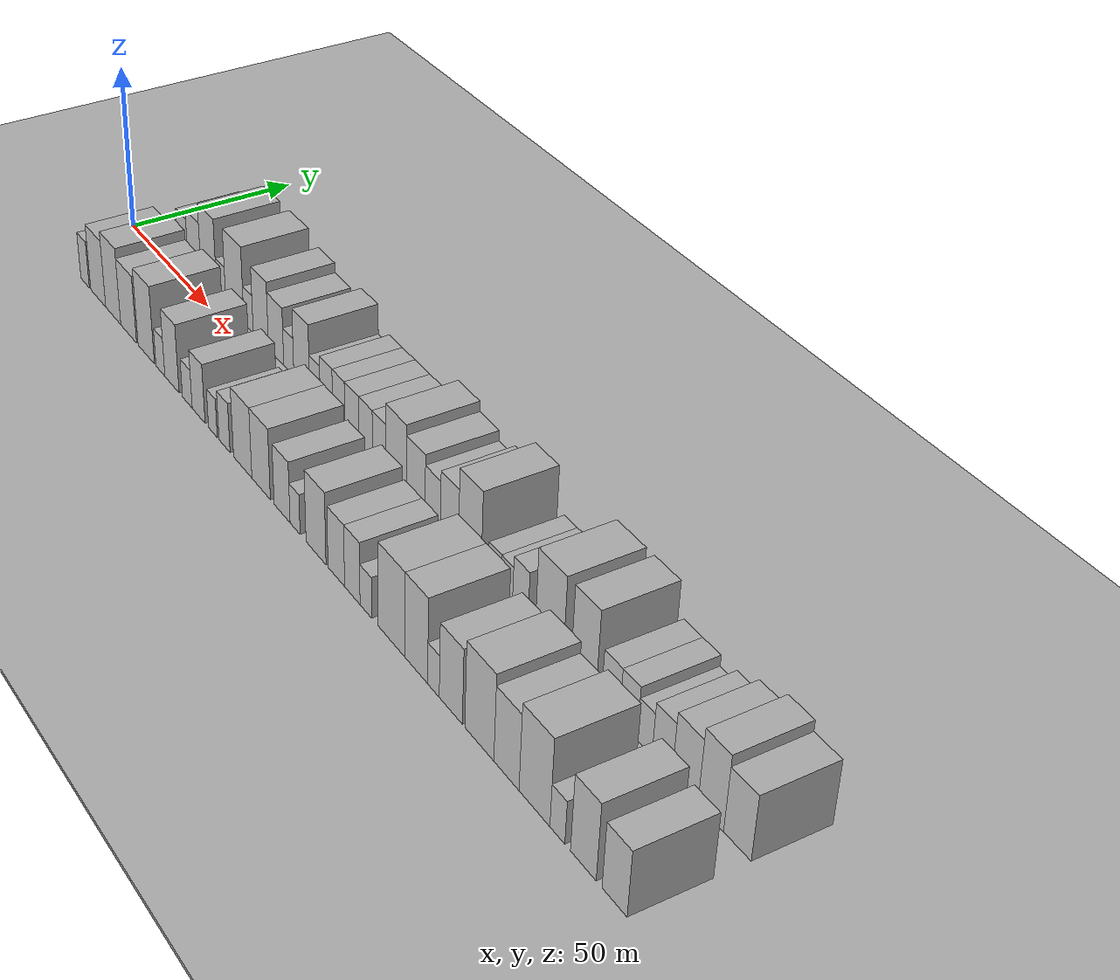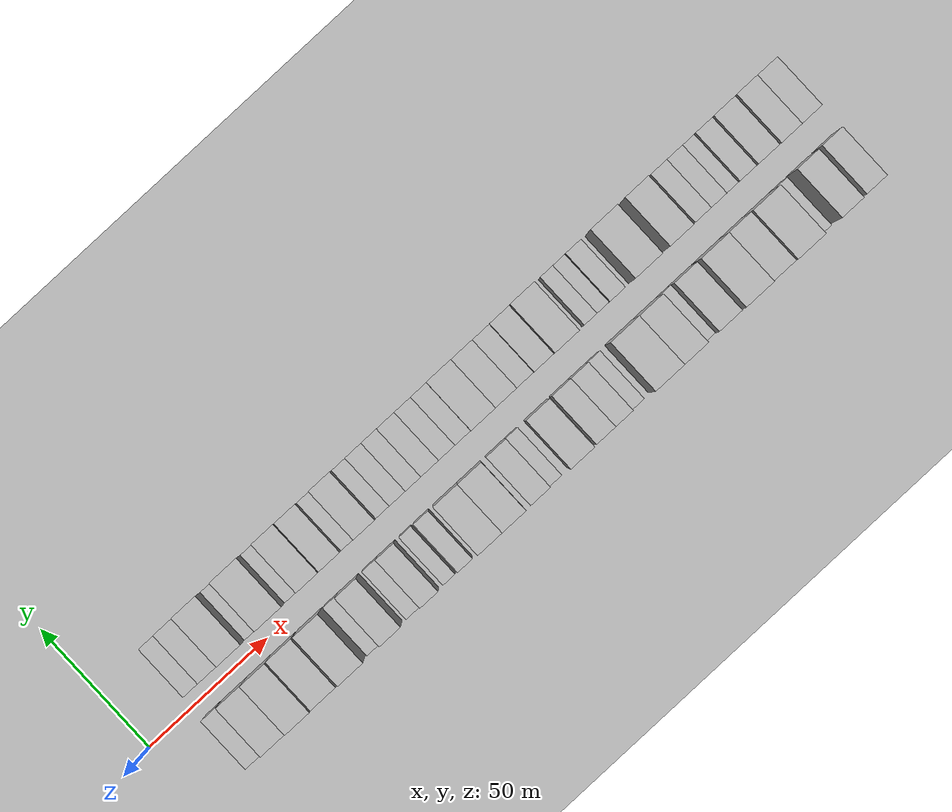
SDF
<?xml version="1.0" encoding="utf-8"?>

<sdf version="1.6">

   <world name="default">

      <gui fullscreen="0">

         <camera name="user_camera">

            <pose>-15 0 4.57585 0 0 0</pose>

            <view_controller>orbit</view_controller>

         </camera>

      </gui>

      <scene>

         <sky>

           <clouds>

             <speed>12</speed>

           </clouds>

         </sky>

         <ambient>0.4 0.4 0.4 1</ambient>

         <background>0.7 0.7 0.7 1</background>

         <shadows>1</shadows>

      </scene>

      <gravity>0 0 -9.8066</gravity>

      <magnetic_field>6e-06 2.3e-05 -4.2e-05</magnetic_field>

      <physics default="0" name="default_physics" type="ode">

         <ode>

            <solver>

               <type>quick</type>

               <iters>10</iters>

               <sor>1.0</sor>

               <use_dynamic_moi_rescaling>0</use_dynamic_moi_rescaling>

            </solver>

            <constraints>

               <cfm>0</cfm>

               <erp>0.2</erp>

               <contact_max_correcting_vel>100</contact_max_correcting_vel>

               <contact_surface_layer>0.001</contact_surface_layer>

            </constraints>

         </ode>

         <max_step_size>0.004</max_step_size>

         <real_time_factor>1</real_time_factor>

         <real_time_update_rate>250</real_time_update_rate>

      </physics>

      <light name="sun" type="directional">

         <cast_shadows>1</cast_shadows>

         <pose>0 0 10 0 0 0</pose>

         <diffuse>0.8 0.8 0.8 1</diffuse>

         <specular>0.2 0.2 0.2 1</specular>

         <attenuation>

            <range>1000</range>

            <constant>0.9</constant>

            <linear>0.01</linear>

            <quadratic>0.001</quadratic>

         </attenuation>

         <direction>-0.5 0.1 -0.9</direction>

      </light>

      <include>

         <name>ground_plane_1</name>

         <uri>model://HANNAS_ground_plane</uri>

         <pose>0 0 0  0 0 0</pose>

      </include>

      <include>

         <name>ground_plane_2</name>

         <uri>model://HANNAS_ground_plane</uri>

         <pose>100 0 0  0 0 0</pose>

      </include>

      <model name="building_1">

         <static>1</static>

         <pose frame="">24.3070 14.5000 0 0.000000 0.000000 1.570796</pose>

         <link name="link">

            <pose frame="">0 0 7.50 0 0 0</pose>

            <collision name="collision">

               <geometry>

                  <box>

                     <size>20.0000 6.6139 15.0000</size>

                  </box>

               </geometry>

               <max_contacts>10</max_contacts>

               <surface>

                  <contact>

                     <ode/>

                  </contact>

                  <bounce/>

                  <friction>

                     <torsional>

                        <ode/>

                     </torsional>

                     <ode/>

                  </friction>

               </surface>

            </collision>

            <visual name="visual">

               <cast_shadows>0</cast_shadows>

               <geometry>

                  <box>

                     <size>20.0000 6.6139 15.0000</size>

                  </box>

               </geometry>

               <material>

                  <script>

                     <uri>model://HANNAS_wall/materials/scripts</uri>

                     <uri>model://HANNAS_wall/materials/textures</uri>

                     <name>vrc/HANNAS_wall</name>

                  </script>

               </material>

            </visual>

            <self_collide>0</self_collide>

            <enable_wind>0</enable_wind>

            <kinematic>0</kinematic>

         </link>

      </model>

      <model name="building_2">

         <static>1</static>

         <pose frame="">31.9232 14.5000 0 0.000000 0.000000 1.570796</pose>

         <link name="link">

            <pose frame="">0 0 9.00 0 0 0</pose>

            <collision name="collision">

               <geometry>

                  <box>

                     <size>20.0000 8.6186 18.0000</size>

                  </box>

               </geometry>

               <max_contacts>10</max_contacts>

               <surface>

                  <contact>

                     <ode/>

                  </contact>

                  <bounce/>

                  <friction>

                     <torsional>

                        <ode/>

                     </torsional>

                     <ode/>

                  </friction>

               </surface>

            </collision>

            <visual name="visual">

               <cast_shadows>0</cast_shadows>

               <geometry>

                  <box>

                     <size>20.0000 8.6186 18.0000</size>

                  </box>

               </geometry>

               <material>

                  <script>

                     <uri>model://HANNAS_wall/materials/scripts</uri>

                     <uri>model://HANNAS_wall/materials/textures</uri>

                     <name>vrc/HANNAS_wall</name>

                  </script>

               </material>

            </visual>

            <self_collide>0</self_collide>

            <enable_wind>0</enable_wind>

            <kinematic>0</kinematic>

         </link>

      </model>

      <model name="building_3">

         <static>1</static>

         <pose frame="">41.1928 14.5000 0 0.000000 0.000000 1.570796</pose>

         <link name="link">

            <pose frame="">0 0 12.00 0 0 0</pose>

            <collision name="collision">

               <geometry>

                  <box>

                     <size>20.0000 9.9206 24.0000</size>

                  </box>

               </geometry>

               <max_contacts>10</max_contacts>

               <surface>

                  <contact>

                     <ode/>

                  </contact>

                  <bounce/>

                  <friction>

                     <torsional>

                        <ode/>

                     </torsional>

                     <ode/>

                  </friction>

               </surface>

            </collision>

            <visual name="visual">

               <cast_shadows>0</cast_shadows>

               <geometry>

                  <box>

                     <size>20.0000 9.9206 24.0000</size>

                  </box>

               </geometry>

               <material>

                  <script>

                     <uri>model://HANNAS_wall/materials/scripts</uri>

                     <uri>model://HANNAS_wall/materials/textures</uri>

                     <name>vrc/HANNAS_wall</name>

                  </script>

               </material>

            </visual>

            <self_collide>0</self_collide>

            <enable_wind>0</enable_wind>

            <kinematic>0</kinematic>

         </link>

      </model>

      <model name="building_4">

         <static>1</static>

         <pose frame="">48.9845 14.5000 0 0.000000 0.000000 1.570796</pose>

         <link name="link">

            <pose frame="">0 0 6.00 0 0 0</pose>

            <collision name="collision">

               <geometry>

                  <box>

                     <size>20.0000 5.6629 12.0000</size>

                  </box>

               </geometry>

               <max_contacts>10</max_contacts>

               <surface>

                  <contact>

                     <ode/>

                  </contact>

                  <bounce/>

                  <friction>

                     <torsional>

                        <ode/>

                     </torsional>

                     <ode/>

                  </friction>

               </surface>

            </collision>

            <visual name="visual">

               <cast_shadows>0</cast_shadows>

               <geometry>

                  <box>

                     <size>20.0000 5.6629 12.0000</size>

                  </box>

               </geometry>

               <material>

                  <script>

                     <uri>model://HANNAS_wall/materials/scripts</uri>

                     <uri>model://HANNAS_wall/materials/textures</uri>

                     <name>vrc/HANNAS_wall</name>

                  </script>

               </material>

            </visual>

            <self_collide>0</self_collide>

            <enable_wind>0</enable_wind>

            <kinematic>0</kinematic>

         </link>

      </model>

      <model name="building_5">

         <static>1</static>

         <pose frame="">57.3648 14.5000 0 0.000000 0.000000 1.570796</pose>

         <link name="link">

            <pose frame="">0 0 12.00 0 0 0</pose>

            <collision name="collision">

               <geometry>

                  <box>

                     <size>20.0000 11.0977 24.0000</size>

                  </box>

               </geometry>

               <max_contacts>10</max_contacts>

               <surface>

                  <contact>

                     <ode/>

                  </contact>

                  <bounce/>

                  <friction>

                     <torsional>

                        <ode/>

                     </torsional>

                     <ode/>

                  </friction>

               </surface>

            </collision>

            <visual name="visual">

               <cast_shadows>0</cast_shadows>

               <geometry>

                  <box>

                     <size>20.0000 11.0977 24.0000</size>

                  </box>

               </geometry>

               <material>

                  <script>

                     <uri>model://HANNAS_wall/materials/scripts</uri>

                     <uri>model://HANNAS_wall/materials/textures</uri>

                     <name>vrc/HANNAS_wall</name>

                  </script>

               </material>

            </visual>

            <self_collide>0</self_collide>

            <enable_wind>0</enable_wind>

            <kinematic>0</kinematic>

         </link>

      </model>

      <model name="building_6">

         <static>1</static>

         <pose frame="">65.7075 14.5000 0 0.000000 0.000000 1.570796</pose>

         <link name="link">

            <pose frame="">0 0 6.00 0 0 0</pose>

            <collision name="collision">

               <geometry>

                  <box>

                     <size>20.0000 5.5876 12.0000</size>

                  </box>

               </geometry>

               <max_contacts>10</max_contacts>

               <surface>

                  <contact>

                     <ode/>

                  </contact>

                  <bounce/>

                  <friction>

                     <torsional>

                        <ode/>

                     </torsional>

                     <ode/>

                  </friction>

               </surface>

            </collision>

            <visual name="visual">

               <cast_shadows>0</cast_shadows>

               <geometry>

                  <box>

                     <size>20.0000 5.5876 12.0000</size>

                  </box>

               </geometry>

               <material>

                  <script>

                     <uri>model://HANNAS_wall/materials/scripts</uri>

                     <uri>model://HANNAS_wall/materials/textures</uri>

                     <name>vrc/HANNAS_wall</name>

                  </script>

               </material>

            </visual>

            <self_collide>0</self_collide>

            <enable_wind>0</enable_wind>

            <kinematic>0</kinematic>

         </link>

      </model>

      <model name="building_7">

         <static>1</static>

         <pose frame="">73.0353 14.5000 0 0.000000 0.000000 1.570796</pose>

         <link name="link">

            <pose frame="">0 0 10.50 0 0 0</pose>

            <collision name="collision">

               <geometry>

                  <box>

                     <size>20.0000 9.0681 21.0000</size>

                  </box>

               </geometry>

               <max_contacts>10</max_contacts>

               <surface>

                  <contact>

                     <ode/>

                  </contact>

                  <bounce/>

                  <friction>

                     <torsional>

                        <ode/>

                     </torsional>

                     <ode/>

                  </friction>

               </surface>

            </collision>

            <visual name="visual">

               <cast_shadows>0</cast_shadows>

               <geometry>

                  <box>

                     <size>20.0000 9.0681 21.0000</size>

                  </box>

               </geometry>

               <material>

                  <script>

                     <uri>model://HANNAS_wall/materials/scripts</uri>

                     <uri>model://HANNAS_wall/materials/textures</uri>

                     <name>vrc/HANNAS_wall</name>

                  </script>

               </material>

            </visual>

            <self_collide>0</self_collide>

            <enable_wind>0</enable_wind>

            <kinematic>0</kinematic>

         </link>

      </model>

      <model name="building_8">

         <static>1</static>

         <pose frame="">81.9653 14.5000 0 0.000000 0.000000 1.570796</pose>

         <link name="link">

            <pose frame="">0 0 9.00 0 0 0</pose>

            <collision name="collision">

               <geometry>

                  <box>

                     <size>20.0000 8.7918 18.0000</size>

                  </box>

               </geometry>

               <max_contacts>10</max_contacts>

               <surface>

                  <contact>

                     <ode/>

                  </contact>

                  <bounce/>

                  <friction>

                     <torsional>

                        <ode/>

                     </torsional>

                     <ode/>

                  </friction>

               </surface>

            </collision>

            <visual name="visual">

               <cast_shadows>0</cast_shadows>

               <geometry>

                  <box>

                     <size>20.0000 8.7918 18.0000</size>

                  </box>

               </geometry>

               <material>

                  <script>

                     <uri>model://HANNAS_wall/materials/scripts</uri>

                     <uri>model://HANNAS_wall/materials/textures</uri>

                     <name>vrc/HANNAS_wall</name>

                  </script>

               </material>

            </visual>

            <self_collide>0</self_collide>

            <enable_wind>0</enable_wind>

            <kinematic>0</kinematic>

         </link>

      </model>

      <model name="building_9">

         <static>1</static>

         <pose frame="">89.2294 14.5000 0 0.000000 0.000000 1.570796</pose>

         <link name="link">

            <pose frame="">0 0 6.00 0 0 0</pose>

            <collision name="collision">

               <geometry>

                  <box>

                     <size>20.0000 5.7364 12.0000</size>

                  </box>

               </geometry>

               <max_contacts>10</max_contacts>

               <surface>

                  <contact>

                     <ode/>

                  </contact>

                  <bounce/>

                  <friction>

                     <torsional>

                        <ode/>

                     </torsional>

                     <ode/>

                  </friction>

               </surface>

            </collision>

            <visual name="visual">

               <cast_shadows>0</cast_shadows>

               <geometry>

                  <box>

                     <size>20.0000 5.7364 12.0000</size>

                  </box>

               </geometry>

               <material>

                  <script>

                     <uri>model://HANNAS_wall/materials/scripts</uri>

                     <uri>model://HANNAS_wall/materials/textures</uri>

                     <name>vrc/HANNAS_wall</name>

                  </script>

               </material>

            </visual>

            <self_collide>0</self_collide>

            <enable_wind>0</enable_wind>

            <kinematic>0</kinematic>

         </link>

      </model>

      <model name="building_10">

         <static>1</static>

         <pose frame="">96.5183 14.5000 0 0.000000 0.000000 1.570796</pose>

         <link name="link">

            <pose frame="">0 0 10.50 0 0 0</pose>

            <collision name="collision">

               <geometry>

                  <box>

                     <size>20.0000 8.8415 21.0000</size>

                  </box>

               </geometry>

               <max_contacts>10</max_contacts>

               <surface>

                  <contact>

                     <ode/>

                  </contact>

                  <bounce/>

                  <friction>

                     <torsional>

                        <ode/>

                     </torsional>

                     <ode/>

                  </friction>

               </surface>

            </collision>

            <visual name="visual">

               <cast_shadows>0</cast_shadows>

               <geometry>

                  <box>

                     <size>20.0000 8.8415 21.0000</size>

                  </box>

               </geometry>

               <material>

                  <script>

                     <uri>model://HANNAS_wall/materials/scripts</uri>

                     <uri>model://HANNAS_wall/materials/textures</uri>

                     <name>vrc/HANNAS_wall</name>

                  </script>

               </material>

            </visual>

            <self_collide>0</self_collide>

            <enable_wind>0</enable_wind>

            <kinematic>0</kinematic>

         </link>

      </model>

      <model name="building_11">

         <static>1</static>

         <pose frame="">103.8284 14.5000 0 0.000000 0.000000 1.570796</pose>

         <link name="link">

            <pose frame="">0 0 6.00 0 0 0</pose>

            <collision name="collision">

               <geometry>

                  <box>

                     <size>20.0000 5.7787 12.0000</size>

                  </box>

               </geometry>

               <max_contacts>10</max_contacts>

               <surface>

                  <contact>

                     <ode/>

                  </contact>

                  <bounce/>

                  <friction>

                     <torsional>

                        <ode/>

                     </torsional>

                     <ode/>

                  </friction>

               </surface>

            </collision>

            <visual name="visual">

               <cast_shadows>0</cast_shadows>

               <geometry>

                  <box>

                     <size>20.0000 5.7787 12.0000</size>

                  </box>

               </geometry>

               <material>

                  <script>

                     <uri>model://HANNAS_wall/materials/scripts</uri>

                     <uri>model://HANNAS_wall/materials/textures</uri>

                     <name>vrc/HANNAS_wall</name>

                  </script>

               </material>

            </visual>

            <self_collide>0</self_collide>

            <enable_wind>0</enable_wind>

            <kinematic>0</kinematic>

         </link>

      </model>

      <model name="building_12">

         <static>1</static>

         <pose frame="">110.0669 14.5000 0 0.000000 0.000000 1.570796</pose>

         <link name="link">

            <pose frame="">0 0 7.50 0 0 0</pose>

            <collision name="collision">

               <geometry>

                  <box>

                     <size>20.0000 6.6983 15.0000</size>

                  </box>

               </geometry>

               <max_contacts>10</max_contacts>

               <surface>

                  <contact>

                     <ode/>

                  </contact>

                  <bounce/>

                  <friction>

                     <torsional>

                        <ode/>

                     </torsional>

                     <ode/>

                  </friction>

               </surface>

            </collision>

            <visual name="visual">

               <cast_shadows>0</cast_shadows>

               <geometry>

                  <box>

                     <size>20.0000 6.6983 15.0000</size>

                  </box>

               </geometry>

               <material>

                  <script>

                     <uri>model://HANNAS_wall/materials/scripts</uri>

                     <uri>model://HANNAS_wall/materials/textures</uri>

                     <name>vrc/HANNAS_wall</name>

                  </script>

               </material>

            </visual>

            <self_collide>0</self_collide>

            <enable_wind>0</enable_wind>

            <kinematic>0</kinematic>

         </link>

      </model>

      <model name="building_13">

         <static>1</static>

         <pose frame="">116.6327 14.5000 0 0.000000 0.000000 1.570796</pose>

         <link name="link">

            <pose frame="">0 0 7.50 0 0 0</pose>

            <collision name="collision">

               <geometry>

                  <box>

                     <size>20.0000 6.4335 15.0000</size>

                  </box>

               </geometry>

               <max_contacts>10</max_contacts>

               <surface>

                  <contact>

                     <ode/>

                  </contact>

                  <bounce/>

                  <friction>

                     <torsional>

                        <ode/>

                     </torsional>

                     <ode/>

                  </friction>

               </surface>

            </collision>

            <visual name="visual">

               <cast_shadows>0</cast_shadows>

               <geometry>

                  <box>

                     <size>20.0000 6.4335 15.0000</size>

                  </box>

               </geometry>

               <material>

                  <script>

                     <uri>model://HANNAS_wall/materials/scripts</uri>

                     <uri>model://HANNAS_wall/materials/textures</uri>

                     <name>vrc/HANNAS_wall</name>

                  </script>

               </material>

            </visual>

            <self_collide>0</self_collide>

            <enable_wind>0</enable_wind>

            <kinematic>0</kinematic>

         </link>

      </model>

      <model name="building_14">

         <static>1</static>

         <pose frame="">123.5289 14.5000 0 0.000000 0.000000 1.570796</pose>

         <link name="link">

            <pose frame="">0 0 7.50 0 0 0</pose>

            <collision name="collision">

               <geometry>

                  <box>

                     <size>20.0000 7.3588 15.0000</size>

                  </box>

               </geometry>

               <max_contacts>10</max_contacts>

               <surface>

                  <contact>

                     <ode/>

                  </contact>

                  <bounce/>

                  <friction>

                     <torsional>

                        <ode/>

                     </torsional>

                     <ode/>

                  </friction>

               </surface>

            </collision>

            <visual name="visual">

               <cast_shadows>0</cast_shadows>

               <geometry>

                  <box>

                     <size>20.0000 7.3588 15.0000</size>

                  </box>

               </geometry>

               <material>

                  <script>

                     <uri>model://HANNAS_wall/materials/scripts</uri>

                     <uri>model://HANNAS_wall/materials/textures</uri>

                     <name>vrc/HANNAS_wall</name>

                  </script>

               </material>

            </visual>

            <self_collide>0</self_collide>

            <enable_wind>0</enable_wind>

            <kinematic>0</kinematic>

         </link>

      </model>

      <model name="building_15">

         <static>1</static>

         <pose frame="">130.6145 14.5000 0 0.000000 0.000000 1.570796</pose>

         <link name="link">

            <pose frame="">0 0 7.50 0 0 0</pose>

            <collision name="collision">

               <geometry>

                  <box>

                     <size>20.0000 6.8125 15.0000</size>

                  </box>

               </geometry>

               <max_contacts>10</max_contacts>

               <surface>

                  <contact>

                     <ode/>

                  </contact>

                  <bounce/>

                  <friction>

                     <torsional>

                        <ode/>

                     </torsional>

                     <ode/>

                  </friction>

               </surface>

            </collision>

            <visual name="visual">

               <cast_shadows>0</cast_shadows>

               <geometry>

                  <box>

                     <size>20.0000 6.8125 15.0000</size>

                  </box>

               </geometry>

               <material>

                  <script>

                     <uri>model://HANNAS_wall/materials/scripts</uri>

                     <uri>model://HANNAS_wall/materials/textures</uri>

                     <name>vrc/HANNAS_wall</name>

                  </script>

               </material>

            </visual>

            <self_collide>0</self_collide>

            <enable_wind>0</enable_wind>

            <kinematic>0</kinematic>

         </link>

      </model>

      <model name="building_16">

         <static>1</static>

         <pose frame="">137.3013 14.5000 0 0.000000 0.000000 1.570796</pose>

         <link name="link">

            <pose frame="">0 0 7.50 0 0 0</pose>

            <collision name="collision">

               <geometry>

                  <box>

                     <size>20.0000 6.5612 15.0000</size>

                  </box>

               </geometry>

               <max_contacts>10</max_contacts>

               <surface>

                  <contact>

                     <ode/>

                  </contact>

                  <bounce/>

                  <friction>

                     <torsional>

                        <ode/>

                     </torsional>

                     <ode/>

                  </friction>

               </surface>

            </collision>

            <visual name="visual">

               <cast_shadows>0</cast_shadows>

               <geometry>

                  <box>

                     <size>20.0000 6.5612 15.0000</size>

                  </box>

               </geometry>

               <material>

                  <script>

                     <uri>model://HANNAS_wall/materials/scripts</uri>

                     <uri>model://HANNAS_wall/materials/textures</uri>

                     <name>vrc/HANNAS_wall</name>

                  </script>

               </material>

            </visual>

            <self_collide>0</self_collide>

            <enable_wind>0</enable_wind>

            <kinematic>0</kinematic>

         </link>

      </model>

      <model name="building_17">

         <static>1</static>

         <pose frame="">145.6593 14.5000 0 0.000000 0.000000 1.570796</pose>

         <link name="link">

            <pose frame="">0 0 10.50 0 0 0</pose>

            <collision name="collision">

               <geometry>

                  <box>

                     <size>20.0000 10.1548 21.0000</size>

                  </box>

               </geometry>

               <max_contacts>10</max_contacts>

               <surface>

                  <contact>

                     <ode/>

                  </contact>

                  <bounce/>

                  <friction>

                     <torsional>

                        <ode/>

                     </torsional>

                     <ode/>

                  </friction>

               </surface>

            </collision>

            <visual name="visual">

               <cast_shadows>0</cast_shadows>

               <geometry>

                  <box>

                     <size>20.0000 10.1548 21.0000</size>

                  </box>

               </geometry>

               <material>

                  <script>

                     <uri>model://HANNAS_wall/materials/scripts</uri>

                     <uri>model://HANNAS_wall/materials/textures</uri>

                     <name>vrc/HANNAS_wall</name>

                  </script>

               </material>

            </visual>

            <self_collide>0</self_collide>

            <enable_wind>0</enable_wind>

            <kinematic>0</kinematic>

         </link>

      </model>

      <model name="building_18">

         <static>1</static>

         <pose frame="">155.1751 14.5000 0 0.000000 0.000000 1.570796</pose>

         <link name="link">

            <pose frame="">0 0 9.00 0 0 0</pose>

            <collision name="collision">

               <geometry>

                  <box>

                     <size>20.0000 8.8768 18.0000</size>

                  </box>

               </geometry>

               <max_contacts>10</max_contacts>

               <surface>

                  <contact>

                     <ode/>

                  </contact>

                  <bounce/>

                  <friction>

                     <torsional>

                        <ode/>

                     </torsional>

                     <ode/>

                  </friction>

               </surface>

            </collision>

            <visual name="visual">

               <cast_shadows>0</cast_shadows>

               <geometry>

                  <box>

                     <size>20.0000 8.8768 18.0000</size>

                  </box>

               </geometry>

               <material>

                  <script>

                     <uri>model://HANNAS_wall/materials/scripts</uri>

                     <uri>model://HANNAS_wall/materials/textures</uri>

                     <name>vrc/HANNAS_wall</name>

                  </script>

               </material>

            </visual>

            <self_collide>0</self_collide>

            <enable_wind>0</enable_wind>

            <kinematic>0</kinematic>

         </link>

      </model>

      <model name="building_19">

         <static>1</static>

         <pose frame="">163.1832 14.5000 0 0.000000 0.000000 1.570796</pose>

         <link name="link">

            <pose frame="">0 0 7.50 0 0 0</pose>

            <collision name="collision">

               <geometry>

                  <box>

                     <size>20.0000 7.1393 15.0000</size>

                  </box>

               </geometry>

               <max_contacts>10</max_contacts>

               <surface>

                  <contact>

                     <ode/>

                  </contact>

                  <bounce/>

                  <friction>

                     <torsional>

                        <ode/>

                     </torsional>

                     <ode/>

                  </friction>

               </surface>

            </collision>

            <visual name="visual">

               <cast_shadows>0</cast_shadows>

               <geometry>

                  <box>

                     <size>20.0000 7.1393 15.0000</size>

                  </box>

               </geometry>

               <material>

                  <script>

                     <uri>model://HANNAS_wall/materials/scripts</uri>

                     <uri>model://HANNAS_wall/materials/textures</uri>

                     <name>vrc/HANNAS_wall</name>

                  </script>

               </material>

            </visual>

            <self_collide>0</self_collide>

            <enable_wind>0</enable_wind>

            <kinematic>0</kinematic>

         </link>

      </model>

      <model name="building_20">

         <static>1</static>

         <pose frame="">170.8533 14.5000 0 0.000000 0.000000 1.570796</pose>

         <link name="link">

            <pose frame="">0 0 9.00 0 0 0</pose>

            <collision name="collision">

               <geometry>

                  <box>

                     <size>20.0000 8.2009 18.0000</size>

                  </box>

               </geometry>

               <max_contacts>10</max_contacts>

               <surface>

                  <contact>

                     <ode/>

                  </contact>

                  <bounce/>

                  <friction>

                     <torsional>

                        <ode/>

                     </torsional>

                     <ode/>

                  </friction>

               </surface>

            </collision>

            <visual name="visual">

               <cast_shadows>0</cast_shadows>

               <geometry>

                  <box>

                     <size>20.0000 8.2009 18.0000</size>

                  </box>

               </geometry>

               <material>

                  <script>

                     <uri>model://HANNAS_wall/materials/scripts</uri>

                     <uri>model://HANNAS_wall/materials/textures</uri>

                     <name>vrc/HANNAS_wall</name>

                  </script>

               </material>

            </visual>

            <self_collide>0</self_collide>

            <enable_wind>0</enable_wind>

            <kinematic>0</kinematic>

         </link>

      </model>

      <model name="building_21">

         <static>1</static>

         <pose frame="">180.0035 14.5000 0 0.000000 0.000000 1.570796</pose>

         <link name="link">

            <pose frame="">0 0 12.00 0 0 0</pose>

            <collision name="collision">

               <geometry>

                  <box>

                     <size>20.0000 10.0996 24.0000</size>

                  </box>

               </geometry>

               <max_contacts>10</max_contacts>

               <surface>

                  <contact>

                     <ode/>

                  </contact>

                  <bounce/>

                  <friction>

                     <torsional>

                        <ode/>

                     </torsional>

                     <ode/>

                  </friction>

               </surface>

            </collision>

            <visual name="visual">

               <cast_shadows>0</cast_shadows>

               <geometry>

                  <box>

                     <size>20.0000 10.0996 24.0000</size>

                  </box>

               </geometry>

               <material>

                  <script>

                     <uri>model://HANNAS_wall/materials/scripts</uri>

                     <uri>model://HANNAS_wall/materials/textures</uri>

                     <name>vrc/HANNAS_wall</name>

                  </script>

               </material>

            </visual>

            <self_collide>0</self_collide>

            <enable_wind>0</enable_wind>

            <kinematic>0</kinematic>

         </link>

      </model>

      <model name="building_22">

         <static>1</static>

         <pose frame="">190.7245 14.5000 0 0.000000 0.000000 1.570796</pose>

         <link name="link">

            <pose frame="">0 0 6.00 0 0 0</pose>

            <collision name="collision">

               <geometry>

                  <box>

                     <size>20.0000 5.3423 12.0000</size>

                  </box>

               </geometry>

               <max_contacts>10</max_contacts>

               <surface>

                  <contact>

                     <ode/>

                  </contact>

                  <bounce/>

                  <friction>

                     <torsional>

                        <ode/>

                     </torsional>

                     <ode/>

                  </friction>

               </surface>

            </collision>

            <visual name="visual">

               <cast_shadows>0</cast_shadows>

               <geometry>

                  <box>

                     <size>20.0000 5.3423 12.0000</size>

                  </box>

               </geometry>

               <material>

                  <script>

                     <uri>model://HANNAS_wall/materials/scripts</uri>

                     <uri>model://HANNAS_wall/materials/textures</uri>

                     <name>vrc/HANNAS_wall</name>

                  </script>

               </material>

            </visual>

            <self_collide>0</self_collide>

            <enable_wind>0</enable_wind>

            <kinematic>0</kinematic>

         </link>

      </model>

      <model name="building_23">

         <static>1</static>

         <pose frame="">195.9058 14.5000 0 0.000000 0.000000 1.570796</pose>

         <link name="link">

            <pose frame="">0 0 6.00 0 0 0</pose>

            <collision name="collision">

               <geometry>

                  <box>

                     <size>20.0000 5.0203 12.0000</size>

                  </box>

               </geometry>

               <max_contacts>10</max_contacts>

               <surface>

                  <contact>

                     <ode/>

                  </contact>

                  <bounce/>

                  <friction>

                     <torsional>

                        <ode/>

                     </torsional>

                     <ode/>

                  </friction>

               </surface>

            </collision>

            <visual name="visual">

               <cast_shadows>0</cast_shadows>

               <geometry>

                  <box>

                     <size>20.0000 5.0203 12.0000</size>

                  </box>

               </geometry>

               <material>

                  <script>

                     <uri>model://HANNAS_wall/materials/scripts</uri>

                     <uri>model://HANNAS_wall/materials/textures</uri>

                     <name>vrc/HANNAS_wall</name>

                  </script>

               </material>

            </visual>

            <self_collide>0</self_collide>

            <enable_wind>0</enable_wind>

            <kinematic>0</kinematic>

         </link>

      </model>

      <model name="building_24">

         <static>1</static>

         <pose frame="">201.6565 14.5000 0 0.000000 0.000000 1.570796</pose>

         <link name="link">

            <pose frame="">0 0 7.50 0 0 0</pose>

            <collision name="collision">

               <geometry>

                  <box>

                     <size>20.0000 6.4810 15.0000</size>

                  </box>

               </geometry>

               <max_contacts>10</max_contacts>

               <surface>

                  <contact>

                     <ode/>

                  </contact>

                  <bounce/>

                  <friction>

                     <torsional>

                        <ode/>

                     </torsional>

                     <ode/>

                  </friction>

               </surface>

            </collision>

            <visual name="visual">

               <cast_shadows>0</cast_shadows>

               <geometry>

                  <box>

                     <size>20.0000 6.4810 15.0000</size>

                  </box>

               </geometry>

               <material>

                  <script>

                     <uri>model://HANNAS_wall/materials/scripts</uri>

                     <uri>model://HANNAS_wall/materials/textures</uri>

                     <name>vrc/HANNAS_wall</name>

                  </script>

               </material>

            </visual>

            <self_collide>0</self_collide>

            <enable_wind>0</enable_wind>

            <kinematic>0</kinematic>

         </link>

      </model>

      <model name="building_25">

         <static>1</static>

         <pose frame="">213.5023 14.5000 0 0.000000 0.000000 1.570796</pose>

         <link name="link">

            <pose frame="">0 0 12.00 0 0 0</pose>

            <collision name="collision">

               <geometry>

                  <box>

                     <size>20.0000 11.2107 24.0000</size>

                  </box>

               </geometry>

               <max_contacts>10</max_contacts>

               <surface>

                  <contact>

                     <ode/>

                  </contact>

                  <bounce/>

                  <friction>

                     <torsional>

                        <ode/>

                     </torsional>

                     <ode/>

                  </friction>

               </surface>

            </collision>

            <visual name="visual">

               <cast_shadows>0</cast_shadows>

               <geometry>

                  <box>

                     <size>20.0000 11.2107 24.0000</size>

                  </box>

               </geometry>

               <material>

                  <script>

                     <uri>model://HANNAS_wall/materials/scripts</uri>

                     <uri>model://HANNAS_wall/materials/textures</uri>

                     <name>vrc/HANNAS_wall</name>

                  </script>

               </material>

            </visual>

            <self_collide>0</self_collide>

            <enable_wind>0</enable_wind>

            <kinematic>0</kinematic>

         </link>

      </model>

      <model name="building_26">

         <static>1</static>

         <pose frame="">226.9615 14.5000 0 0.000000 0.000000 1.570796</pose>

         <link name="link">

            <pose frame="">0 0 12.00 0 0 0</pose>

            <collision name="collision">

               <geometry>

                  <box>

                     <size>20.0000 9.7077 24.0000</size>

                  </box>

               </geometry>

               <max_contacts>10</max_contacts>

               <surface>

                  <contact>

                     <ode/>

                  </contact>

                  <bounce/>

                  <friction>

                     <torsional>

                        <ode/>

                     </torsional>

                     <ode/>

                  </friction>

               </surface>

            </collision>

            <visual name="visual">

               <cast_shadows>0</cast_shadows>

               <geometry>

                  <box>

                     <size>20.0000 9.7077 24.0000</size>

                  </box>

               </geometry>

               <material>

                  <script>

                     <uri>model://HANNAS_wall/materials/scripts</uri>

                     <uri>model://HANNAS_wall/materials/textures</uri>

                     <name>vrc/HANNAS_wall</name>

                  </script>

               </material>

            </visual>

            <self_collide>0</self_collide>

            <enable_wind>0</enable_wind>

            <kinematic>0</kinematic>

         </link>

      </model>

      <model name="building_27">

         <static>1</static>

         <pose frame="">237.1932 14.5000 0 0.000000 0.000000 1.570796</pose>

         <link name="link">

            <pose frame="">0 0 7.50 0 0 0</pose>

            <collision name="collision">

               <geometry>

                  <box>

                     <size>20.0000 6.7558 15.0000</size>

                  </box>

               </geometry>

               <max_contacts>10</max_contacts>

               <surface>

                  <contact>

                     <ode/>

                  </contact>

                  <bounce/>

                  <friction>

                     <torsional>

                        <ode/>

                     </torsional>

                     <ode/>

                  </friction>

               </surface>

            </collision>

            <visual name="visual">

               <cast_shadows>0</cast_shadows>

               <geometry>

                  <box>

                     <size>20.0000 6.7558 15.0000</size>

                  </box>

               </geometry>

               <material>

                  <script>

                     <uri>model://HANNAS_wall/materials/scripts</uri>

                     <uri>model://HANNAS_wall/materials/textures</uri>

                     <name>vrc/HANNAS_wall</name>

                  </script>

               </material>

            </visual>

            <self_collide>0</self_collide>

            <enable_wind>0</enable_wind>

            <kinematic>0</kinematic>

         </link>

      </model>

      <model name="building_28">

         <static>1</static>

         <pose frame="">243.8081 14.5000 0 0.000000 0.000000 1.570796</pose>

         <link name="link">

            <pose frame="">0 0 7.50 0 0 0</pose>

            <collision name="collision">

               <geometry>

                  <box>

                     <size>20.0000 6.4741 15.0000</size>

                  </box>

               </geometry>

               <max_contacts>10</max_contacts>

               <surface>

                  <contact>

                     <ode/>

                  </contact>

                  <bounce/>

                  <friction>

                     <torsional>

                        <ode/>

                     </torsional>

                     <ode/>

                  </friction>

               </surface>

            </collision>

            <visual name="visual">

               <cast_shadows>0</cast_shadows>

               <geometry>

                  <box>

                     <size>20.0000 6.4741 15.0000</size>

                  </box>

               </geometry>

               <material>

                  <script>

                     <uri>model://HANNAS_wall/materials/scripts</uri>

                     <uri>model://HANNAS_wall/materials/textures</uri>

                     <name>vrc/HANNAS_wall</name>

                  </script>

               </material>

            </visual>

            <self_collide>0</self_collide>

            <enable_wind>0</enable_wind>

            <kinematic>0</kinematic>

         </link>

      </model>

      <model name="building_29">

         <static>1</static>

         <pose frame="">249.7371 14.5000 0 0.000000 0.000000 1.570796</pose>

         <link name="link">

            <pose frame="">0 0 6.00 0 0 0</pose>

            <collision name="collision">

               <geometry>

                  <box>

                     <size>20.0000 5.3839 12.0000</size>

                  </box>

               </geometry>

               <max_contacts>10</max_contacts>

               <surface>

                  <contact>

                     <ode/>

                  </contact>

                  <bounce/>

                  <friction>

                     <torsional>

                        <ode/>

                     </torsional>

                     <ode/>

                  </friction>

               </surface>

            </collision>

            <visual name="visual">

               <cast_shadows>0</cast_shadows>

               <geometry>

                  <box>

                     <size>20.0000 5.3839 12.0000</size>

                  </box>

               </geometry>

               <material>

                  <script>

                     <uri>model://HANNAS_wall/materials/scripts</uri>

                     <uri>model://HANNAS_wall/materials/textures</uri>

                     <name>vrc/HANNAS_wall</name>

                  </script>

               </material>

            </visual>

            <self_collide>0</self_collide>

            <enable_wind>0</enable_wind>

            <kinematic>0</kinematic>

         </link>

      </model>

      <model name="building_30">

         <static>1</static>

         <pose frame="">255.9594 14.5000 0 0.000000 0.000000 1.570796</pose>

         <link name="link">

            <pose frame="">0 0 7.50 0 0 0</pose>

            <collision name="collision">

               <geometry>

                  <box>

                     <size>20.0000 7.0605 15.0000</size>

                  </box>

               </geometry>

               <max_contacts>10</max_contacts>

               <surface>

                  <contact>

                     <ode/>

                  </contact>

                  <bounce/>

                  <friction>

                     <torsional>

                        <ode/>

                     </torsional>

                     <ode/>

                  </friction>

               </surface>

            </collision>

            <visual name="visual">

               <cast_shadows>0</cast_shadows>

               <geometry>

                  <box>

                     <size>20.0000 7.0605 15.0000</size>

                  </box>

               </geometry>

               <material>

                  <script>

                     <uri>model://HANNAS_wall/materials/scripts</uri>

                     <uri>model://HANNAS_wall/materials/textures</uri>

                     <name>vrc/HANNAS_wall</name>

                  </script>

               </material>

            </visual>

            <self_collide>0</self_collide>

            <enable_wind>0</enable_wind>

            <kinematic>0</kinematic>

         </link>

      </model>

      <model name="building_31">

         <static>1</static>

         <pose frame="">263.9150 14.5000 0 0.000000 0.000000 1.570796</pose>

         <link name="link">

            <pose frame="">0 0 9.00 0 0 0</pose>

            <collision name="collision">

               <geometry>

                  <box>

                     <size>20.0000 8.8508 18.0000</size>

                  </box>

               </geometry>

               <max_contacts>10</max_contacts>

               <surface>

                  <contact>

                     <ode/>

                  </contact>

                  <bounce/>

                  <friction>

                     <torsional>

                        <ode/>

                     </torsional>

                     <ode/>

                  </friction>

               </surface>

            </collision>

            <visual name="visual">

               <cast_shadows>0</cast_shadows>

               <geometry>

                  <box>

                     <size>20.0000 8.8508 18.0000</size>

                  </box>

               </geometry>

               <material>

                  <script>

                     <uri>model://HANNAS_wall/materials/scripts</uri>

                     <uri>model://HANNAS_wall/materials/textures</uri>

                     <name>vrc/HANNAS_wall</name>

                  </script>

               </material>

            </visual>

            <self_collide>0</self_collide>

            <enable_wind>0</enable_wind>

            <kinematic>0</kinematic>

         </link>

      </model>

      <model name="building_32">

         <static>1</static>

         <pose frame="">272.6241 14.5000 0 0.000000 0.000000 1.570796</pose>

         <link name="link">

            <pose frame="">0 0 10.50 0 0 0</pose>

            <collision name="collision">

               <geometry>

                  <box>

                     <size>20.0000 8.5672 21.0000</size>

                  </box>

               </geometry>

               <max_contacts>10</max_contacts>

               <surface>

                  <contact>

                     <ode/>

                  </contact>

                  <bounce/>

                  <friction>

                     <torsional>

                        <ode/>

                     </torsional>

                     <ode/>

                  </friction>

               </surface>

            </collision>

            <visual name="visual">

               <cast_shadows>0</cast_shadows>

               <geometry>

                  <box>

                     <size>20.0000 8.5672 21.0000</size>

                  </box>

               </geometry>

               <material>

                  <script>

                     <uri>model://HANNAS_wall/materials/scripts</uri>

                     <uri>model://HANNAS_wall/materials/textures</uri>

                     <name>vrc/HANNAS_wall</name>

                  </script>

               </material>

            </visual>

            <self_collide>0</self_collide>

            <enable_wind>0</enable_wind>

            <kinematic>0</kinematic>

         </link>

      </model>

      <model name="building_33">

         <static>1</static>

         <pose frame="">281.3903 14.5000 0 0.000000 0.000000 1.570796</pose>

         <link name="link">

            <pose frame="">0 0 9.00 0 0 0</pose>

            <collision name="collision">

               <geometry>

                  <box>

                     <size>20.0000 8.9652 18.0000</size>

                  </box>

               </geometry>

               <max_contacts>10</max_contacts>

               <surface>

                  <contact>

                     <ode/>

                  </contact>

                  <bounce/>

                  <friction>

                     <torsional>

                        <ode/>

                     </torsional>

                     <ode/>

                  </friction>

               </surface>

            </collision>

            <visual name="visual">

               <cast_shadows>0</cast_shadows>

               <geometry>

                  <box>

                     <size>20.0000 8.9652 18.0000</size>

                  </box>

               </geometry>

               <material>

                  <script>

                     <uri>model://HANNAS_wall/materials/scripts</uri>

                     <uri>model://HANNAS_wall/materials/textures</uri>

                     <name>vrc/HANNAS_wall</name>

                  </script>

               </material>

            </visual>

            <self_collide>0</self_collide>

            <enable_wind>0</enable_wind>

            <kinematic>0</kinematic>

         </link>

      </model>

      <model name="building_34">

         <static>1</static>

         <pose frame="">23.0090 -14.5000 0 0.000000 0.000000 1.570796</pose>

         <link name="link">

            <pose frame="">0 0 7.50 0 0 0</pose>

            <collision name="collision">

               <geometry>

                  <box>

                     <size>20.0000 6.0180 15.0000</size>

                  </box>

               </geometry>

               <max_contacts>10</max_contacts>

               <surface>

                  <contact>

                     <ode/>

                  </contact>

                  <bounce/>

                  <friction>

                     <torsional>

                        <ode/>

                     </torsional>

                     <ode/>

                  </friction>

               </surface>

            </collision>

            <visual name="visual">

               <cast_shadows>0</cast_shadows>

               <geometry>

                  <box>

                     <size>20.0000 6.0180 15.0000</size>

                  </box>

               </geometry>

               <material>

                  <script>

                     <uri>model://HANNAS_wall/materials/scripts</uri>

                     <uri>model://HANNAS_wall/materials/textures</uri>

                     <name>vrc/HANNAS_wall</name>

                  </script>

               </material>

            </visual>

            <self_collide>0</self_collide>

            <enable_wind>0</enable_wind>

            <kinematic>0</kinematic>

         </link>

      </model>

      <model name="building_35">

         <static>1</static>

         <pose frame="">32.1826 -14.5000 0 0.000000 0.000000 1.570796</pose>

         <link name="link">

            <pose frame="">0 0 10.50 0 0 0</pose>

            <collision name="collision">

               <geometry>

                  <box>

                     <size>20.0000 10.3293 21.0000</size>

                  </box>

               </geometry>

               <max_contacts>10</max_contacts>

               <surface>

                  <contact>

                     <ode/>

                  </contact>

                  <bounce/>

                  <friction>

                     <torsional>

                        <ode/>

                     </torsional>

                     <ode/>

                  </friction>

               </surface>

            </collision>

            <visual name="visual">

               <cast_shadows>0</cast_shadows>

               <geometry>

                  <box>

                     <size>20.0000 10.3293 21.0000</size>

                  </box>

               </geometry>

               <material>

                  <script>

                     <uri>model://HANNAS_wall/materials/scripts</uri>

                     <uri>model://HANNAS_wall/materials/textures</uri>

                     <name>vrc/HANNAS_wall</name>

                  </script>

               </material>

            </visual>

            <self_collide>0</self_collide>

            <enable_wind>0</enable_wind>

            <kinematic>0</kinematic>

         </link>

      </model>

      <model name="building_36">

         <static>1</static>

         <pose frame="">42.4412 -14.5000 0 0.000000 0.000000 1.570796</pose>

         <link name="link">

            <pose frame="">0 0 12.00 0 0 0</pose>

            <collision name="collision">

               <geometry>

                  <box>

                     <size>20.0000 10.1880 24.0000</size>

                  </box>

               </geometry>

               <max_contacts>10</max_contacts>

               <surface>

                  <contact>

                     <ode/>

                  </contact>

                  <bounce/>

                  <friction>

                     <torsional>

                        <ode/>

                     </torsional>

                     <ode/>

                  </friction>

               </surface>

            </collision>

            <visual name="visual">

               <cast_shadows>0</cast_shadows>

               <geometry>

                  <box>

                     <size>20.0000 10.1880 24.0000</size>

                  </box>

               </geometry>

               <material>

                  <script>

                     <uri>model://HANNAS_wall/materials/scripts</uri>

                     <uri>model://HANNAS_wall/materials/textures</uri>

                     <name>vrc/HANNAS_wall</name>

                  </script>

               </material>

            </visual>

            <self_collide>0</self_collide>

            <enable_wind>0</enable_wind>

            <kinematic>0</kinematic>

         </link>

      </model>

      <model name="building_37">

         <static>1</static>

         <pose frame="">52.7492 -14.5000 0 0.000000 0.000000 1.570796</pose>

         <link name="link">

            <pose frame="">0 0 10.50 0 0 0</pose>

            <collision name="collision">

               <geometry>

                  <box>

                     <size>20.0000 10.4279 21.0000</size>

                  </box>

               </geometry>

               <max_contacts>10</max_contacts>

               <surface>

                  <contact>

                     <ode/>

                  </contact>

                  <bounce/>

                  <friction>

                     <torsional>

                        <ode/>

                     </torsional>

                     <ode/>

                  </friction>

               </surface>

            </collision>

            <visual name="visual">

               <cast_shadows>0</cast_shadows>

               <geometry>

                  <box>

                     <size>20.0000 10.4279 21.0000</size>

                  </box>

               </geometry>

               <material>

                  <script>

                     <uri>model://HANNAS_wall/materials/scripts</uri>

                     <uri>model://HANNAS_wall/materials/textures</uri>

                     <name>vrc/HANNAS_wall</name>

                  </script>

               </material>

            </visual>

            <self_collide>0</self_collide>

            <enable_wind>0</enable_wind>

            <kinematic>0</kinematic>

         </link>

      </model>

      <model name="building_38">

         <static>1</static>

         <pose frame="">64.1693 -14.5000 0 0.000000 0.000000 1.570796</pose>

         <link name="link">

            <pose frame="">0 0 12.00 0 0 0</pose>

            <collision name="collision">

               <geometry>

                  <box>

                     <size>20.0000 10.4124 24.0000</size>

                  </box>

               </geometry>

               <max_contacts>10</max_contacts>

               <surface>

                  <contact>

                     <ode/>

                  </contact>

                  <bounce/>

                  <friction>

                     <torsional>

                        <ode/>

                     </torsional>

                     <ode/>

                  </friction>

               </surface>

            </collision>

            <visual name="visual">

               <cast_shadows>0</cast_shadows>

               <geometry>

                  <box>

                     <size>20.0000 10.4124 24.0000</size>

                  </box>

               </geometry>

               <material>

                  <script>

                     <uri>model://HANNAS_wall/materials/scripts</uri>

                     <uri>model://HANNAS_wall/materials/textures</uri>

                     <name>vrc/HANNAS_wall</name>

                  </script>

               </material>

            </visual>

            <self_collide>0</self_collide>

            <enable_wind>0</enable_wind>

            <kinematic>0</kinematic>

         </link>

      </model>

      <model name="building_39">

         <static>1</static>

         <pose frame="">73.1631 -14.5000 0 0.000000 0.000000 1.570796</pose>

         <link name="link">

            <pose frame="">0 0 6.00 0 0 0</pose>

            <collision name="collision">

               <geometry>

                  <box>

                     <size>20.0000 5.5752 12.0000</size>

                  </box>

               </geometry>

               <max_contacts>10</max_contacts>

               <surface>

                  <contact>

                     <ode/>

                  </contact>

                  <bounce/>

                  <friction>

                     <torsional>

                        <ode/>

                     </torsional>

                     <ode/>

                  </friction>

               </surface>

            </collision>

            <visual name="visual">

               <cast_shadows>0</cast_shadows>

               <geometry>

                  <box>

                     <size>20.0000 5.5752 12.0000</size>

                  </box>

               </geometry>

               <material>

                  <script>

                     <uri>model://HANNAS_wall/materials/scripts</uri>

                     <uri>model://HANNAS_wall/materials/textures</uri>

                     <name>vrc/HANNAS_wall</name>

                  </script>

               </material>

            </visual>

            <self_collide>0</self_collide>

            <enable_wind>0</enable_wind>

            <kinematic>0</kinematic>

         </link>

      </model>

      <model name="building_40">

         <static>1</static>

         <pose frame="">80.3299 -14.5000 0 0.000000 0.000000 1.570796</pose>

         <link name="link">

            <pose frame="">0 0 10.50 0 0 0</pose>

            <collision name="collision">

               <geometry>

                  <box>

                     <size>20.0000 8.7584 21.0000</size>

                  </box>

               </geometry>

               <max_contacts>10</max_contacts>

               <surface>

                  <contact>

                     <ode/>

                  </contact>

                  <bounce/>

                  <friction>

                     <torsional>

                        <ode/>

                     </torsional>

                     <ode/>

                  </friction>

               </surface>

            </collision>

            <visual name="visual">

               <cast_shadows>0</cast_shadows>

               <geometry>

                  <box>

                     <size>20.0000 8.7584 21.0000</size>

                  </box>

               </geometry>

               <material>

                  <script>

                     <uri>model://HANNAS_wall/materials/scripts</uri>

                     <uri>model://HANNAS_wall/materials/textures</uri>

                     <name>vrc/HANNAS_wall</name>

                  </script>

               </material>

            </visual>

            <self_collide>0</self_collide>

            <enable_wind>0</enable_wind>

            <kinematic>0</kinematic>

         </link>

      </model>

      <model name="building_41">

         <static>1</static>

         <pose frame="">89.6402 -14.5000 0 0.000000 0.000000 1.570796</pose>

         <link name="link">

            <pose frame="">0 0 6.00 0 0 0</pose>

            <collision name="collision">

               <geometry>

                  <box>

                     <size>20.0000 5.8622 12.0000</size>

                  </box>

               </geometry>

               <max_contacts>10</max_contacts>

               <surface>

                  <contact>

                     <ode/>

                  </contact>

                  <bounce/>

                  <friction>

                     <torsional>

                        <ode/>

                     </torsional>

                     <ode/>

                  </friction>

               </surface>

            </collision>

            <visual name="visual">

               <cast_shadows>0</cast_shadows>

               <geometry>

                  <box>

                     <size>20.0000 5.8622 12.0000</size>

                  </box>

               </geometry>

               <material>

                  <script>

                     <uri>model://HANNAS_wall/materials/scripts</uri>

                     <uri>model://HANNAS_wall/materials/textures</uri>

                     <name>vrc/HANNAS_wall</name>

                  </script>

               </material>

            </visual>

            <self_collide>0</self_collide>

            <enable_wind>0</enable_wind>

            <kinematic>0</kinematic>

         </link>

      </model>

      <model name="building_42">

         <static>1</static>

         <pose frame="">96.3569 -14.5000 0 0.000000 0.000000 1.570796</pose>

         <link name="link">

            <pose frame="">0 0 9.00 0 0 0</pose>

            <collision name="collision">

               <geometry>

                  <box>

                     <size>20.0000 7.5712 18.0000</size>

                  </box>

               </geometry>

               <max_contacts>10</max_contacts>

               <surface>

                  <contact>

                     <ode/>

                  </contact>

                  <bounce/>

                  <friction>

                     <torsional>

                        <ode/>

                     </torsional>

                     <ode/>

                  </friction>

               </surface>

            </collision>

            <visual name="visual">

               <cast_shadows>0</cast_shadows>

               <geometry>

                  <box>

                     <size>20.0000 7.5712 18.0000</size>

                  </box>

               </geometry>

               <material>

                  <script>

                     <uri>model://HANNAS_wall/materials/scripts</uri>

                     <uri>model://HANNAS_wall/materials/textures</uri>

                     <name>vrc/HANNAS_wall</name>

                  </script>

               </material>

            </visual>

            <self_collide>0</self_collide>

            <enable_wind>0</enable_wind>

            <kinematic>0</kinematic>

         </link>

      </model>

      <model name="building_43">

         <static>1</static>

         <pose frame="">104.6766 -14.5000 0 0.000000 0.000000 1.570796</pose>

         <link name="link">

            <pose frame="">0 0 6.00 0 0 0</pose>

            <collision name="collision">

               <geometry>

                  <box>

                     <size>20.0000 5.0681 12.0000</size>

                  </box>

               </geometry>

               <max_contacts>10</max_contacts>

               <surface>

                  <contact>

                     <ode/>

                  </contact>

                  <bounce/>

                  <friction>

                     <torsional>

                        <ode/>

                     </torsional>

                     <ode/>

                  </friction>

               </surface>

            </collision>

            <visual name="visual">

               <cast_shadows>0</cast_shadows>

               <geometry>

                  <box>

                     <size>20.0000 5.0681 12.0000</size>

                  </box>

               </geometry>

               <material>

                  <script>

                     <uri>model://HANNAS_wall/materials/scripts</uri>

                     <uri>model://HANNAS_wall/materials/textures</uri>

                     <name>vrc/HANNAS_wall</name>

                  </script>

               </material>

            </visual>

            <self_collide>0</self_collide>

            <enable_wind>0</enable_wind>

            <kinematic>0</kinematic>

         </link>

      </model>

      <model name="building_44">

         <static>1</static>

         <pose frame="">111.3216 -14.5000 0 0.000000 0.000000 1.570796</pose>

         <link name="link">

            <pose frame="">0 0 7.50 0 0 0</pose>

            <collision name="collision">

               <geometry>

                  <box>

                     <size>20.0000 6.2220 15.0000</size>

                  </box>

               </geometry>

               <max_contacts>10</max_contacts>

               <surface>

                  <contact>

                     <ode/>

                  </contact>

                  <bounce/>

                  <friction>

                     <torsional>

                        <ode/>

                     </torsional>

                     <ode/>

                  </friction>

               </surface>

            </collision>

            <visual name="visual">

               <cast_shadows>0</cast_shadows>

               <geometry>

                  <box>

                     <size>20.0000 6.2220 15.0000</size>

                  </box>

               </geometry>

               <material>

                  <script>

                     <uri>model://HANNAS_wall/materials/scripts</uri>

                     <uri>model://HANNAS_wall/materials/textures</uri>

                     <name>vrc/HANNAS_wall</name>

                  </script>

               </material>

            </visual>

            <self_collide>0</self_collide>

            <enable_wind>0</enable_wind>

            <kinematic>0</kinematic>

         </link>

      </model>

      <model name="building_45">

         <static>1</static>

         <pose frame="">121.4785 -14.5000 0 0.000000 0.000000 1.570796</pose>

         <link name="link">

            <pose frame="">0 0 10.50 0 0 0</pose>

            <collision name="collision">

               <geometry>

                  <box>

                     <size>20.0000 10.0919 21.0000</size>

                  </box>

               </geometry>

               <max_contacts>10</max_contacts>

               <surface>

                  <contact>

                     <ode/>

                  </contact>

                  <bounce/>

                  <friction>

                     <torsional>

                        <ode/>

                     </torsional>

                     <ode/>

                  </friction>

               </surface>

            </collision>

            <visual name="visual">

               <cast_shadows>0</cast_shadows>

               <geometry>

                  <box>

                     <size>20.0000 10.0919 21.0000</size>

                  </box>

               </geometry>

               <material>

                  <script>

                     <uri>model://HANNAS_wall/materials/scripts</uri>

                     <uri>model://HANNAS_wall/materials/textures</uri>

                     <name>vrc/HANNAS_wall</name>

                  </script>

               </material>

            </visual>

            <self_collide>0</self_collide>

            <enable_wind>0</enable_wind>

            <kinematic>0</kinematic>

         </link>

      </model>

      <model name="building_46">

         <static>1</static>

         <pose frame="">131.4741 -14.5000 0 0.000000 0.000000 1.570796</pose>

         <link name="link">

            <pose frame="">0 0 10.50 0 0 0</pose>

            <collision name="collision">

               <geometry>

                  <box>

                     <size>20.0000 9.8993 21.0000</size>

                  </box>

               </geometry>

               <max_contacts>10</max_contacts>

               <surface>

                  <contact>

                     <ode/>

                  </contact>

                  <bounce/>

                  <friction>

                     <torsional>

                        <ode/>

                     </torsional>

                     <ode/>

                  </friction>

               </surface>

            </collision>

            <visual name="visual">

               <cast_shadows>0</cast_shadows>

               <geometry>

                  <box>

                     <size>20.0000 9.8993 21.0000</size>

                  </box>

               </geometry>

               <material>

                  <script>

                     <uri>model://HANNAS_wall/materials/scripts</uri>

                     <uri>model://HANNAS_wall/materials/textures</uri>

                     <name>vrc/HANNAS_wall</name>

                  </script>

               </material>

            </visual>

            <self_collide>0</self_collide>

            <enable_wind>0</enable_wind>

            <kinematic>0</kinematic>

         </link>

      </model>

      <model name="building_47">

         <static>1</static>

         <pose frame="">142.5558 -14.5000 0 0.000000 0.000000 1.570796</pose>

         <link name="link">

            <pose frame="">0 0 9.00 0 0 0</pose>

            <collision name="collision">

               <geometry>

                  <box>

                     <size>20.0000 8.2641 18.0000</size>

                  </box>

               </geometry>

               <max_contacts>10</max_contacts>

               <surface>

                  <contact>

                     <ode/>

                  </contact>

                  <bounce/>

                  <friction>

                     <torsional>

                        <ode/>

                     </torsional>

                     <ode/>

                  </friction>

               </surface>

            </collision>

            <visual name="visual">

               <cast_shadows>0</cast_shadows>

               <geometry>

                  <box>

                     <size>20.0000 8.2641 18.0000</size>

                  </box>

               </geometry>

               <material>

                  <script>

                     <uri>model://HANNAS_wall/materials/scripts</uri>

                     <uri>model://HANNAS_wall/materials/textures</uri>

                     <name>vrc/HANNAS_wall</name>

                  </script>

               </material>

            </visual>

            <self_collide>0</self_collide>

            <enable_wind>0</enable_wind>

            <kinematic>0</kinematic>

         </link>

      </model>

      <model name="building_48">

         <static>1</static>

         <pose frame="">149.2443 -14.5000 0 0.000000 0.000000 1.570796</pose>

         <link name="link">

            <pose frame="">0 0 6.00 0 0 0</pose>

            <collision name="collision">

               <geometry>

                  <box>

                     <size>20.0000 5.1128 12.0000</size>

                  </box>

               </geometry>

               <max_contacts>10</max_contacts>

               <surface>

                  <contact>

                     <ode/>

                  </contact>

                  <bounce/>

                  <friction>

                     <torsional>

                        <ode/>

                     </torsional>

                     <ode/>

                  </friction>

               </surface>

            </collision>

            <visual name="visual">

               <cast_shadows>0</cast_shadows>

               <geometry>

                  <box>

                     <size>20.0000 5.1128 12.0000</size>

                  </box>

               </geometry>

               <material>

                  <script>

                     <uri>model://HANNAS_wall/materials/scripts</uri>

                     <uri>model://HANNAS_wall/materials/textures</uri>

                     <name>vrc/HANNAS_wall</name>

                  </script>

               </material>

            </visual>

            <self_collide>0</self_collide>

            <enable_wind>0</enable_wind>

            <kinematic>0</kinematic>

         </link>

      </model>

      <model name="building_49">

         <static>1</static>

         <pose frame="">159.7428 -14.5000 0 0.000000 0.000000 1.570796</pose>

         <link name="link">

            <pose frame="">0 0 10.50 0 0 0</pose>

            <collision name="collision">

               <geometry>

                  <box>

                     <size>20.0000 9.8843 21.0000</size>

                  </box>

               </geometry>

               <max_contacts>10</max_contacts>

               <surface>

                  <contact>

                     <ode/>

                  </contact>

                  <bounce/>

                  <friction>

                     <torsional>

                        <ode/>

                     </torsional>

                     <ode/>

                  </friction>

               </surface>

            </collision>

            <visual name="visual">

               <cast_shadows>0</cast_shadows>

               <geometry>

                  <box>

                     <size>20.0000 9.8843 21.0000</size>

                  </box>

               </geometry>

               <material>

                  <script>

                     <uri>model://HANNAS_wall/materials/scripts</uri>

                     <uri>model://HANNAS_wall/materials/textures</uri>

                     <name>vrc/HANNAS_wall</name>

                  </script>

               </material>

            </visual>

            <self_collide>0</self_collide>

            <enable_wind>0</enable_wind>

            <kinematic>0</kinematic>

         </link>

      </model>

      <model name="building_50">

         <static>1</static>

         <pose frame="">169.6677 -14.5000 0 0.000000 0.000000 1.570796</pose>

         <link name="link">

            <pose frame="">0 0 9.00 0 0 0</pose>

            <collision name="collision">

               <geometry>

                  <box>

                     <size>20.0000 7.9654 18.0000</size>

                  </box>

               </geometry>

               <max_contacts>10</max_contacts>

               <surface>

                  <contact>

                     <ode/>

                  </contact>

                  <bounce/>

                  <friction>

                     <torsional>

                        <ode/>

                     </torsional>

                     <ode/>

                  </friction>

               </surface>

            </collision>

            <visual name="visual">

               <cast_shadows>0</cast_shadows>

               <geometry>

                  <box>

                     <size>20.0000 7.9654 18.0000</size>

                  </box>

               </geometry>

               <material>

                  <script>

                     <uri>model://HANNAS_wall/materials/scripts</uri>

                     <uri>model://HANNAS_wall/materials/textures</uri>

                     <name>vrc/HANNAS_wall</name>

                  </script>

               </material>

            </visual>

            <self_collide>0</self_collide>

            <enable_wind>0</enable_wind>

            <kinematic>0</kinematic>

         </link>

      </model>

      <model name="building_51">

         <static>1</static>

         <pose frame="">177.2809 -14.5000 0 0.000000 0.000000 1.570796</pose>

         <link name="link">

            <pose frame="">0 0 9.00 0 0 0</pose>

            <collision name="collision">

               <geometry>

                  <box>

                     <size>20.0000 7.2611 18.0000</size>

                  </box>

               </geometry>

               <max_contacts>10</max_contacts>

               <surface>

                  <contact>

                     <ode/>

                  </contact>

                  <bounce/>

                  <friction>

                     <torsional>

                        <ode/>

                     </torsional>

                     <ode/>

                  </friction>

               </surface>

            </collision>

            <visual name="visual">

               <cast_shadows>0</cast_shadows>

               <geometry>

                  <box>

                     <size>20.0000 7.2611 18.0000</size>

                  </box>

               </geometry>

               <material>

                  <script>

                     <uri>model://HANNAS_wall/materials/scripts</uri>

                     <uri>model://HANNAS_wall/materials/textures</uri>

                     <name>vrc/HANNAS_wall</name>

                  </script>

               </material>

            </visual>

            <self_collide>0</self_collide>

            <enable_wind>0</enable_wind>

            <kinematic>0</kinematic>

         </link>

      </model>

      <model name="building_52">

         <static>1</static>

         <pose frame="">183.5952 -14.5000 0 0.000000 0.000000 1.570796</pose>

         <link name="link">

            <pose frame="">0 0 6.00 0 0 0</pose>

            <collision name="collision">

               <geometry>

                  <box>

                     <size>20.0000 5.3674 12.0000</size>

                  </box>

               </geometry>

               <max_contacts>10</max_contacts>

               <surface>

                  <contact>

                     <ode/>

                  </contact>

                  <bounce/>

                  <friction>

                     <torsional>

                        <ode/>

                     </torsional>

                     <ode/>

                  </friction>

               </surface>

            </collision>

            <visual name="visual">

               <cast_shadows>0</cast_shadows>

               <geometry>

                  <box>

                     <size>20.0000 5.3674 12.0000</size>

                  </box>

               </geometry>

               <material>

                  <script>

                     <uri>model://HANNAS_wall/materials/scripts</uri>

                     <uri>model://HANNAS_wall/materials/textures</uri>

                     <name>vrc/HANNAS_wall</name>

                  </script>

               </material>

            </visual>

            <self_collide>0</self_collide>

            <enable_wind>0</enable_wind>

            <kinematic>0</kinematic>

         </link>

      </model>

      <model name="building_53">

         <static>1</static>

         <pose frame="">195.2286 -14.5000 0 0.000000 0.000000 1.570796</pose>

         <link name="link">

            <pose frame="">0 0 12.00 0 0 0</pose>

            <collision name="collision">

               <geometry>

                  <box>

                     <size>20.0000 11.8994 24.0000</size>

                  </box>

               </geometry>

               <max_contacts>10</max_contacts>

               <surface>

                  <contact>

                     <ode/>

                  </contact>

                  <bounce/>

                  <friction>

                     <torsional>

                        <ode/>

                     </torsional>

                     <ode/>

                  </friction>

               </surface>

            </collision>

            <visual name="visual">

               <cast_shadows>0</cast_shadows>

               <geometry>

                  <box>

                     <size>20.0000 11.8994 24.0000</size>

                  </box>

               </geometry>

               <material>

                  <script>

                     <uri>model://HANNAS_wall/materials/scripts</uri>

                     <uri>model://HANNAS_wall/materials/textures</uri>

                     <name>vrc/HANNAS_wall</name>

                  </script>

               </material>

            </visual>

            <self_collide>0</self_collide>

            <enable_wind>0</enable_wind>

            <kinematic>0</kinematic>

         </link>

      </model>

      <model name="building_54">

         <static>1</static>

         <pose frame="">206.0644 -14.5000 0 0.000000 0.000000 1.570796</pose>

         <link name="link">

            <pose frame="">0 0 12.00 0 0 0</pose>

            <collision name="collision">

               <geometry>

                  <box>

                     <size>20.0000 9.7721 24.0000</size>

                  </box>

               </geometry>

               <max_contacts>10</max_contacts>

               <surface>

                  <contact>

                     <ode/>

                  </contact>

                  <bounce/>

                  <friction>

                     <torsional>

                        <ode/>

                     </torsional>

                     <ode/>

                  </friction>

               </surface>

            </collision>

            <visual name="visual">

               <cast_shadows>0</cast_shadows>

               <geometry>

                  <box>

                     <size>20.0000 9.7721 24.0000</size>

                  </box>

               </geometry>

               <material>

                  <script>

                     <uri>model://HANNAS_wall/materials/scripts</uri>

                     <uri>model://HANNAS_wall/materials/textures</uri>

                     <name>vrc/HANNAS_wall</name>

                  </script>

               </material>

            </visual>

            <self_collide>0</self_collide>

            <enable_wind>0</enable_wind>

            <kinematic>0</kinematic>

         </link>

      </model>

      <model name="building_55">

         <static>1</static>

         <pose frame="">213.4082 -14.5000 0 0.000000 0.000000 1.570796</pose>

         <link name="link">

            <pose frame="">0 0 6.00 0 0 0</pose>

            <collision name="collision">

               <geometry>

                  <box>

                     <size>20.0000 4.9154 12.0000</size>

                  </box>

               </geometry>

               <max_contacts>10</max_contacts>

               <surface>

                  <contact>

                     <ode/>

                  </contact>

                  <bounce/>

                  <friction>

                     <torsional>

                        <ode/>

                     </torsional>

                     <ode/>

                  </friction>

               </surface>

            </collision>

            <visual name="visual">

               <cast_shadows>0</cast_shadows>

               <geometry>

                  <box>

                     <size>20.0000 4.9154 12.0000</size>

                  </box>

               </geometry>

               <material>

                  <script>

                     <uri>model://HANNAS_wall/materials/scripts</uri>

                     <uri>model://HANNAS_wall/materials/textures</uri>

                     <name>vrc/HANNAS_wall</name>

                  </script>

               </material>

            </visual>

            <self_collide>0</self_collide>

            <enable_wind>0</enable_wind>

            <kinematic>0</kinematic>

         </link>

      </model>

      <model name="building_56">

         <static>1</static>

         <pose frame="">220.6247 -14.5000 0 0.000000 0.000000 1.570796</pose>

         <link name="link">

            <pose frame="">0 0 10.50 0 0 0</pose>

            <collision name="collision">

               <geometry>

                  <box>

                     <size>20.0000 9.5177 21.0000</size>

                  </box>

               </geometry>

               <max_contacts>10</max_contacts>

               <surface>

                  <contact>

                     <ode/>

                  </contact>

                  <bounce/>

                  <friction>

                     <torsional>

                        <ode/>

                     </torsional>

                     <ode/>

                  </friction>

               </surface>

            </collision>

            <visual name="visual">

               <cast_shadows>0</cast_shadows>

               <geometry>

                  <box>

                     <size>20.0000 9.5177 21.0000</size>

                  </box>

               </geometry>

               <material>

                  <script>

                     <uri>model://HANNAS_wall/materials/scripts</uri>

                     <uri>model://HANNAS_wall/materials/textures</uri>

                     <name>vrc/HANNAS_wall</name>

                  </script>

               </material>

            </visual>

            <self_collide>0</self_collide>

            <enable_wind>0</enable_wind>

            <kinematic>0</kinematic>

         </link>

      </model>

      <model name="building_57">

         <static>1</static>

         <pose frame="">232.1522 -14.5000 0 0.000000 0.000000 1.570796</pose>

         <link name="link">

            <pose frame="">0 0 12.00 0 0 0</pose>

            <collision name="collision">

               <geometry>

                  <box>

                     <size>20.0000 11.5373 24.0000</size>

                  </box>

               </geometry>

               <max_contacts>10</max_contacts>

               <surface>

                  <contact>

                     <ode/>

                  </contact>

                  <bounce/>

                  <friction>

                     <torsional>

                        <ode/>

                     </torsional>

                     <ode/>

                  </friction>

               </surface>

            </collision>

            <visual name="visual">

               <cast_shadows>0</cast_shadows>

               <geometry>

                  <box>

                     <size>20.0000 11.5373 24.0000</size>

                  </box>

               </geometry>

               <material>

                  <script>

                     <uri>model://HANNAS_wall/materials/scripts</uri>

                     <uri>model://HANNAS_wall/materials/textures</uri>

                     <name>vrc/HANNAS_wall</name>

                  </script>

               </material>

            </visual>

            <self_collide>0</self_collide>

            <enable_wind>0</enable_wind>

            <kinematic>0</kinematic>

         </link>

      </model>

      <model name="building_58">

         <static>1</static>

         <pose frame="">242.7516 -14.5000 0 0.000000 0.000000 1.570796</pose>

         <link name="link">

            <pose frame="">0 0 10.50 0 0 0</pose>

            <collision name="collision">

               <geometry>

                  <box>

                     <size>20.0000 9.6615 21.0000</size>

                  </box>

               </geometry>

               <max_contacts>10</max_contacts>

               <surface>

                  <contact>

                     <ode/>

                  </contact>

                  <bounce/>

                  <friction>

                     <torsional>

                        <ode/>

                     </torsional>

                     <ode/>

                  </friction>

               </surface>

            </collision>

            <visual name="visual">

               <cast_shadows>0</cast_shadows>

               <geometry>

                  <box>

                     <size>20.0000 9.6615 21.0000</size>

                  </box>

               </geometry>

               <material>

                  <script>

                     <uri>model://HANNAS_wall/materials/scripts</uri>

                     <uri>model://HANNAS_wall/materials/textures</uri>

                     <name>vrc/HANNAS_wall</name>

                  </script>

               </material>

            </visual>

            <self_collide>0</self_collide>

            <enable_wind>0</enable_wind>

            <kinematic>0</kinematic>

         </link>

      </model>

      <model name="building_59">

         <static>1</static>

         <pose frame="">253.3083 -14.5000 0 0.000000 0.000000 1.570796</pose>

         <link name="link">

            <pose frame="">0 0 12.00 0 0 0</pose>

            <collision name="collision">

               <geometry>

                  <box>

                     <size>20.0000 11.4520 24.0000</size>

                  </box>

               </geometry>

               <max_contacts>10</max_contacts>

               <surface>

                  <contact>

                     <ode/>

                  </contact>

                  <bounce/>

                  <friction>

                     <torsional>

                        <ode/>

                     </torsional>

                     <ode/>

                  </friction>

               </surface>

            </collision>

            <visual name="visual">

               <cast_shadows>0</cast_shadows>

               <geometry>

                  <box>

                     <size>20.0000 11.4520 24.0000</size>

                  </box>

               </geometry>

               <material>

                  <script>

                     <uri>model://HANNAS_wall/materials/scripts</uri>

                     <uri>model://HANNAS_wall/materials/textures</uri>

                     <name>vrc/HANNAS_wall</name>

                  </script>

               </material>

            </visual>

            <self_collide>0</self_collide>

            <enable_wind>0</enable_wind>

            <kinematic>0</kinematic>

         </link>

      </model>

      <model name="building_60">

         <static>1</static>

         <pose frame="">261.7323 -14.5000 0 0.000000 0.000000 1.570796</pose>

         <link name="link">

            <pose frame="">0 0 6.00 0 0 0</pose>

            <collision name="collision">

               <geometry>

                  <box>

                     <size>20.0000 5.3960 12.0000</size>

                  </box>

               </geometry>

               <max_contacts>10</max_contacts>

               <surface>

                  <contact>

                     <ode/>

                  </contact>

                  <bounce/>

                  <friction>

                     <torsional>

                        <ode/>

                     </torsional>

                     <ode/>

                  </friction>

               </surface>

            </collision>

            <visual name="visual">

               <cast_shadows>0</cast_shadows>

               <geometry>

                  <box>

                     <size>20.0000 5.3960 12.0000</size>

                  </box>

               </geometry>

               <material>

                  <script>

                     <uri>model://HANNAS_wall/materials/scripts</uri>

                     <uri>model://HANNAS_wall/materials/textures</uri>

                     <name>vrc/HANNAS_wall</name>

                  </script>

               </material>

            </visual>

            <self_collide>0</self_collide>

            <enable_wind>0</enable_wind>

            <kinematic>0</kinematic>

         </link>

      </model>

      <model name="building_61">

         <static>1</static>

         <pose frame="">270.9341 -14.5000 0 0.000000 0.000000 1.570796</pose>

         <link name="link">

            <pose frame="">0 0 10.50 0 0 0</pose>

            <collision name="collision">

               <geometry>

                  <box>

                     <size>20.0000 9.0076 21.0000</size>

                  </box>

               </geometry>

               <max_contacts>10</max_contacts>

               <surface>

                  <contact>

                     <ode/>

                  </contact>

                  <bounce/>

                  <friction>

                     <torsional>

                        <ode/>

                     </torsional>

                     <ode/>

                  </friction>

               </surface>

            </collision>

            <visual name="visual">

               <cast_shadows>0</cast_shadows>

               <geometry>

                  <box>

                     <size>20.0000 9.0076 21.0000</size>

                  </box>

               </geometry>

               <material>

                  <script>

                     <uri>model://HANNAS_wall/materials/scripts</uri>

                     <uri>model://HANNAS_wall/materials/textures</uri>

                     <name>vrc/HANNAS_wall</name>

                  </script>

               </material>

            </visual>

            <self_collide>0</self_collide>

            <enable_wind>0</enable_wind>

            <kinematic>0</kinematic>

         </link>

      </model>

      <model name="building_62">

         <static>1</static>

         <pose frame="">281.6700 -14.5000 0 0.000000 0.000000 1.570796</pose>

         <link name="link">

            <pose frame="">0 0 9.00 0 0 0</pose>

            <collision name="collision">

               <geometry>

                  <box>

                     <size>20.0000 8.4642 18.0000</size>

                  </box>

               </geometry>

               <max_contacts>10</max_contacts>

               <surface>

                  <contact>

                     <ode/>

                  </contact>

                  <bounce/>

                  <friction>

                     <torsional>

                        <ode/>

                     </torsional>

                     <ode/>

                  </friction>

               </surface>

            </collision>

            <visual name="visual">

               <cast_shadows>0</cast_shadows>

               <geometry>

                  <box>

                     <size>20.0000 8.4642 18.0000</size>

                  </box>

               </geometry>

               <material>

                  <script>

                     <uri>model://HANNAS_wall/materials/scripts</uri>

                     <uri>model://HANNAS_wall/materials/textures</uri>

                     <name>vrc/HANNAS_wall</name>

                  </script>

               </material>

            </visual>

            <self_collide>0</self_collide>

            <enable_wind>0</enable_wind>

            <kinematic>0</kinematic>

         </link>

      </model>

   </world>

</sdf>

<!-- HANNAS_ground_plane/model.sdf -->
<sdf version="1.4">
<model name="HANNAS_ground_plane">
  <static>true</static>
    <link name="link">
      <collision name="collision">
        <geometry>
          <plane>
            <normal>0 0 1</normal>
            <size>1000 1000</size>
          </plane>
        </geometry>
        <surface>
          <friction>
            <ode>
              <mu>100</mu>
              <mu2>50</mu2>
            </ode>
          </friction>
        </surface>
      </collision>
      <visual name="visual">
        <cast_shadows>false</cast_shadows>
        <geometry>
          <plane>
            <normal>0 0 1</normal>
            <size>1000 1000</size>
          </plane>
        </geometry>
        <material>
          <script>
            <uri>model://HANNAS_ground_plane/materials/scripts/HANNAS_ground_plane.material</uri>
	    <uri>model://HANNAS_ground_plane/materials/textures</uri>
            <name>HANNASGroundPlane/Image</name>
          </script>
        </material>
      </visual>
    </link>
  </model>
</sdf>
